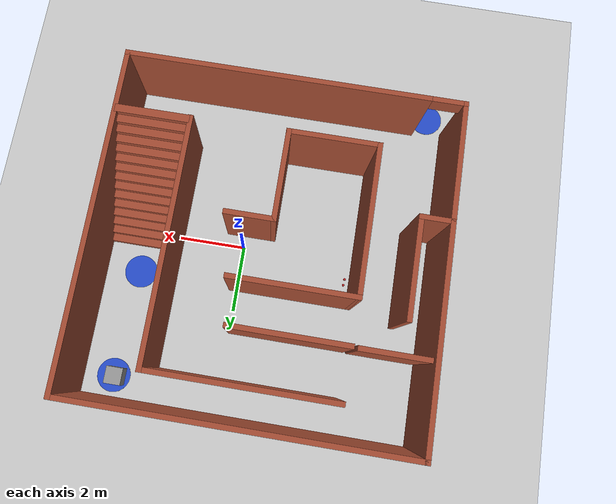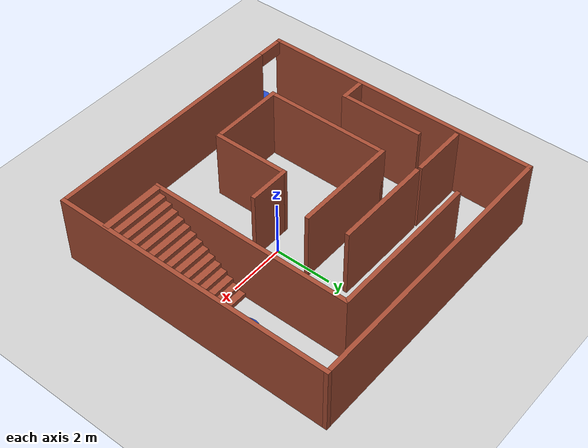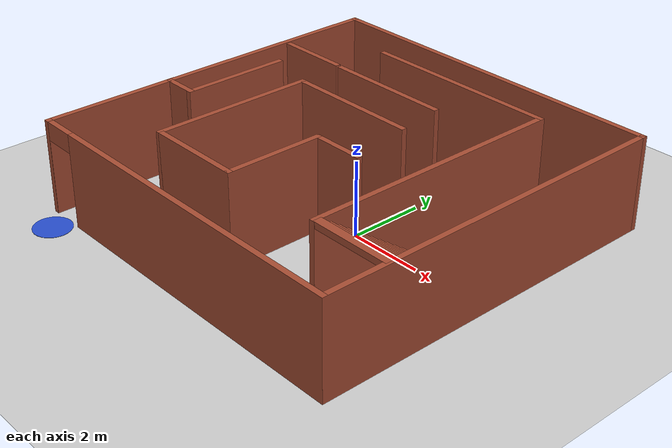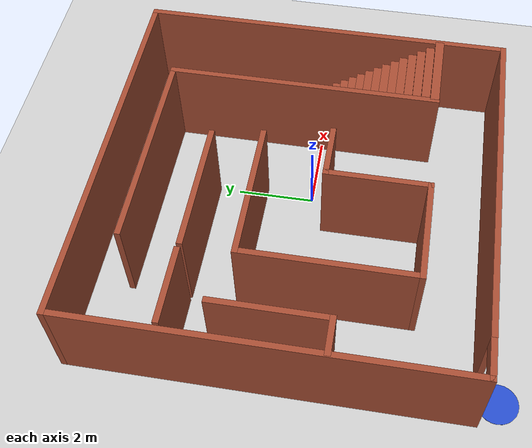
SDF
<sdf version="1.7">
 <world name="default">
  <light name="sun" type="directional">
   <pose>0 0 10 0 -0 0</pose>
   <diffuse>0.8 0.8 0.8 1</diffuse>
   <specular>0.2 0.2 0.2 1</specular>
   <attenuation>
    <range>1000</range>
    <constant>0.9</constant>
    <linear>0.01</linear>
    <quadratic>0.001</quadratic>
   </attenuation>
   <direction>-0.5 0.1 -0.9</direction>
   <spot><inner_angle>0</inner_angle><outer_angle>0</outer_angle><falloff>0</falloff></spot>
  </light>
  <model name="ground_plane">
   <static>1</static>
   <link name="link">
    <collision name="collision">
     <geometry><plane><normal>0 0 1</normal><size>100 100</size></plane></geometry>
     <surface>
      <contact><collide_bitmask>65535</collide_bitmask></contact>
      <friction><ode><mu>100</mu><mu2>50</mu2></ode></friction>
     </surface>
    </collision>
    <visual name="visual">
     <cast_shadows>0</cast_shadows>
     <geometry><plane><normal>0 0 1</normal><size>100 100</size></plane></geometry>
     <material>
      <script><uri>file://media/materials/scripts/gazebo.material</uri><name>Gazebo/Grey</name></script>
     </material>
    </visual>
   </link>
  </model>
  <gravity>0 0 -9.8</gravity>
  <magnetic_field>6e-06 2.3e-05 -4.2e-05</magnetic_field>
  <atmosphere type="adiabatic"/>
  <physics type="ode">
   <max_step_size>0.001</max_step_size>
   <real_time_factor>1</real_time_factor>
   <real_time_update_rate>1000</real_time_update_rate>
  </physics>
  <scene><ambient>0.4 0.4 0.4 1</ambient><background>0.7 0.7 0.7 1</background><shadows>1</shadows></scene>
  <audio><device>default</device></audio>
  <spherical_coordinates>
   <surface_model>EARTH_WGS84</surface_model>
   <latitude_deg>0</latitude_deg>
   <longitude_deg>0</longitude_deg>
   <elevation>0</elevation>
   <heading_deg>0</heading_deg>
  </spherical_coordinates>
  <model name="box">
   <link name="link_1">
    <inertial>
     <mass>875</mass>
     <inertia><ixx>36.4583</ixx><ixy>0</ixy><ixz>0</ixz><iyy>36.4583</iyy><iyz>0</iyz><izz>36.4583</izz></inertia>
    </inertial>
    <pose>1e-06 -5e-06 0 0 -0 0</pose>
    <visual name="visual">
     <geometry><box><size>0.5 0.5 0.5</size></box></geometry>
     <material>
      <lighting>1</lighting>
      <script><uri>file://media/materials/scripts/gazebo.material</uri><name>Gazebo/Grey</name></script>
      <shader type="pixel"><normal_map>__default__</normal_map></shader>
      <ambient>0.3 0.3 0.3 1</ambient>
      <diffuse>0.7 0.7 0.7 1</diffuse>
      <specular>0.01 0.01 0.01 1</specular>
      <emissive>0 0 0 1</emissive>
     </material>
    </visual>
    <collision name="collision">
     <geometry><box><size>0.5 0.5 0.5</size></box></geometry>
     <surface>
      <friction>
       <ode><mu>1</mu><mu2>1</mu2><fdir1>0 0 0</fdir1><slip1>0</slip1><slip2>0</slip2></ode>
       <torsional>
        <coefficient>1</coefficient>
        <patch_radius>0</patch_radius>
        <surface_radius>0</surface_radius>
        <use_patch_radius>1</use_patch_radius>
        <ode><slip>0</slip></ode>
       </torsional>
      </friction>
      <bounce><restitution_coefficient>0</restitution_coefficient><threshold>1e+06</threshold></bounce>
      <contact>
       <collide_without_contact>0</collide_without_contact>
       <collide_without_contact_bitmask>1</collide_without_contact_bitmask>
       <collide_bitmask>1</collide_bitmask>
       <ode>
        <soft_cfm>0</soft_cfm>
        <soft_erp>0.2</soft_erp>
        <kp>1e+13</kp>
        <kd>1</kd>
        <max_vel>0.01</max_vel>
        <min_depth>0</min_depth>
       </ode>
       <bullet>
        <split_impulse>1</split_impulse>
        <split_impulse_penetration_threshold>-0.01</split_impulse_penetration_threshold>
        <soft_cfm>0</soft_cfm>
        <soft_erp>0.2</soft_erp>
        <kp>1e+13</kp>
        <kd>1</kd>
       </bullet>
      </contact>
     </surface>
    </collision>
   </link>
   <static>0</static>
   <pose>3.08441 4.46812 0.255 0 -0 1e-06</pose>
  </model>
  <model name="cricket_ball">
   <link name="link">
    <pose>0 0 0.0375 0 -0 0</pose>
    <inertial>
     <mass>0.1467</mass>
     <inertia>
      <ixx>8.25187e-05</ixx>
      <ixy>0</ixy>
      <ixz>0</ixz>
      <iyy>8.25187e-05</iyy>
      <iyz>0</iyz>
      <izz>8.25187e-05</izz>
     </inertia>
    </inertial>
    <collision name="collision">
     <geometry><sphere><radius>0.0375</radius></sphere></geometry>
     <surface>
      <contact>
       <poissons_ratio>0.347</poissons_ratio>
       <elastic_modulus>8.8e+09</elastic_modulus>
       <ode><kp>100000</kp><kd>100</kd><max_vel>100</max_vel><min_depth>0.001</min_depth></ode>
      </contact>
      <friction>
       <torsional>
        <coefficient>1</coefficient>
        <use_patch_radius>0</use_patch_radius>
        <surface_radius>0.01</surface_radius>
       </torsional>
      </friction>
     </surface>
    </collision>
    <visual name="visual">
     <geometry><sphere><radius>0.0375</radius></sphere></geometry>
     <material>
      <script><uri>file://media/materials/scripts/gazebo.material</uri><name>Gazebo/Red</name></script>
     </material>
    </visual>
    <velocity_decay><linear>0</linear><angular>0.005</angular></velocity_decay>
   </link>
   <pose>-3.24488 0.467417 -0.001014 0 -0 0</pose>
  </model>
  <model name="cricket_ball_0">
   <link name="link">
    <pose>0 0 0.0375 0 -0 0</pose>
    <inertial>
     <mass>0.1467</mass>
     <inertia>
      <ixx>8.25187e-05</ixx>
      <ixy>0</ixy>
      <ixz>0</ixz>
      <iyy>8.25187e-05</iyy>
      <iyz>0</iyz>
      <izz>8.25187e-05</izz>
     </inertia>
    </inertial>
    <collision name="collision">
     <geometry><sphere><radius>0.0375</radius></sphere></geometry>
     <surface>
      <contact>
       <poissons_ratio>0.347</poissons_ratio>
       <elastic_modulus>8.8e+09</elastic_modulus>
       <ode><kp>100000</kp><kd>100</kd><max_vel>100</max_vel><min_depth>0.001</min_depth></ode>
      </contact>
      <friction>
       <torsional>
        <coefficient>1</coefficient>
        <use_patch_radius>0</use_patch_radius>
        <surface_radius>0.01</surface_radius>
       </torsional>
      </friction>
     </surface>
    </collision>
    <visual name="visual">
     <geometry><sphere><radius>0.0375</radius></sphere></geometry>
     <material>
      <script><uri>file://media/materials/scripts/gazebo.material</uri><name>Gazebo/Red</name></script>
     </material>
    </visual>
    <velocity_decay><linear>0</linear><angular>0.005</angular></velocity_decay>
   </link>
   <pose>-3.22979 0.649662 -0.001014 0 -0 0</pose>
  </model>
  <model name="Green_Circle">
   <link name="link_0">
    <inertial>
     <mass>1</mass>
     <inertia><ixx>0.145833</ixx><ixy>0</ixy><ixz>0</ixz><iyy>0.145833</iyy><iyz>0</iyz><izz>0.125</izz></inertia>
    </inertial>
    <visual name="visual">
     <geometry><cylinder><radius>0.5</radius><length>0.01</length></cylinder></geometry>
     <material>
      <lighting>1</lighting>
      <script><uri>file://media/materials/scripts/gazebo.material</uri><name>Gazebo/Blue</name></script>
      <shader type="pixel"><normal_map>__default__</normal_map></shader>
      <ambient>0.18 0.761 0.494 1</ambient>
      <diffuse>0.18 0.761 0.494 1</diffuse>
      <specular>0.18 0.761 0.494 1</specular>
      <emissive>0 0 0 1</emissive>
     </material>
    </visual>
    <collision name="collision">
     <geometry><cylinder><radius>0.5</radius><length>0.01</length></cylinder></geometry>
     <surface>
      <friction>
       <ode><mu>1</mu><mu2>1</mu2><fdir1>0 0 0</fdir1><slip1>0</slip1><slip2>0</slip2></ode>
       <torsional>
        <coefficient>1</coefficient>
        <patch_radius>0</patch_radius>
        <surface_radius>0</surface_radius>
        <use_patch_radius>1</use_patch_radius>
        <ode><slip>0</slip></ode>
       </torsional>
      </friction>
      <bounce><restitution_coefficient>0</restitution_coefficient><threshold>1e+06</threshold></bounce>
      <contact>
       <collide_without_contact>0</collide_without_contact>
       <collide_without_contact_bitmask>1</collide_without_contact_bitmask>
       <collide_bitmask>1</collide_bitmask>
       <ode>
        <soft_cfm>0</soft_cfm>
        <soft_erp>0.2</soft_erp>
        <kp>1e+13</kp>
        <kd>1</kd>
        <max_vel>0.01</max_vel>
        <min_depth>0</min_depth>
       </ode>
       <bullet>
        <split_impulse>1</split_impulse>
        <split_impulse_penetration_threshold>-0.01</split_impulse_penetration_threshold>
        <soft_cfm>0</soft_cfm>
        <soft_erp>0.2</soft_erp>
        <kp>1e+13</kp>
        <kd>1</kd>
       </bullet>
      </contact>
     </surface>
    </collision>
   </link>
   <static>1</static>
   <pose>3.18631 4.46804 0 0 -0 0</pose>
  </model>
  <model name="Red_Circle">
   <link name="link_0">
    <inertial>
     <mass>1</mass>
     <inertia><ixx>0.145833</ixx><ixy>0</ixy><ixz>0</ixz><iyy>0.145833</iyy><iyz>0</iyz><izz>0.125</izz></inertia>
    </inertial>
    <visual name="visual">
     <geometry><cylinder><radius>0.5</radius><length>0.01</length></cylinder></geometry>
     <material>
      <lighting>1</lighting>
      <script><uri>file://media/materials/scripts/gazebo.material</uri><name>Gazebo/Blue</name></script>
      <shader type="pixel"><normal_map>__default__</normal_map></shader>
      <ambient>0.753 0.11 0.157 1</ambient>
      <diffuse>0.753 0.11 0.157 1</diffuse>
      <specular>0.753 0.11 0.157 1</specular>
      <emissive>0 0 0 1</emissive>
     </material>
    </visual>
    <collision name="collision">
     <geometry><cylinder><radius>0.5</radius><length>0.01</length></cylinder></geometry>
     <surface>
      <friction>
       <ode><mu>1</mu><mu2>1</mu2><fdir1>0 0 0</fdir1><slip1>0</slip1><slip2>0</slip2></ode>
       <torsional>
        <coefficient>1</coefficient>
        <patch_radius>0</patch_radius>
        <surface_radius>0</surface_radius>
        <use_patch_radius>1</use_patch_radius>
        <ode><slip>0</slip></ode>
       </torsional>
      </friction>
      <bounce><restitution_coefficient>0</restitution_coefficient><threshold>1e+06</threshold></bounce>
      <contact>
       <collide_without_contact>0</collide_without_contact>
       <collide_without_contact_bitmask>1</collide_without_contact_bitmask>
       <collide_bitmask>1</collide_bitmask>
       <ode>
        <soft_cfm>0</soft_cfm>
        <soft_erp>0.2</soft_erp>
        <kp>1e+13</kp>
        <kd>1</kd>
        <max_vel>0.01</max_vel>
        <min_depth>0</min_depth>
       </ode>
       <bullet>
        <split_impulse>1</split_impulse>
        <split_impulse_penetration_threshold>-0.01</split_impulse_penetration_threshold>
        <soft_cfm>0</soft_cfm>
        <soft_erp>0.2</soft_erp>
        <kp>1e+13</kp>
        <kd>1</kd>
       </bullet>
      </contact>
     </surface>
    </collision>
   </link>
   <static>1</static>
   <pose>3.01972 1.24629 0 0 -0 0</pose>
  </model>
  <model name="Blue_Circle_1">
   <link name="link_0">
    <inertial>
     <mass>1</mass>
     <inertia><ixx>0.145833</ixx><ixy>0</ixy><ixz>0</ixz><iyy>0.145833</iyy><iyz>0</iyz><izz>0.125</izz></inertia>
    </inertial>
    <visual name="visual">
     <geometry><cylinder><radius>0.5</radius><length>0.01</length></cylinder></geometry>
     <material>
      <lighting>1</lighting>
      <script><uri>file://media/materials/scripts/gazebo.material</uri><name>Gazebo/Blue</name></script>
      <shader type="pixel"><normal_map>__default__</normal_map></shader>
      <ambient>0.11 0.443 0.847 1</ambient>
      <diffuse>0.11 0.443 0.847 1</diffuse>
      <specular>0.11 0.443 0.847 1</specular>
      <emissive>0 0 0 1</emissive>
     </material>
    </visual>
    <collision name="collision">
     <geometry><cylinder><radius>0.5</radius><length>0.01</length></cylinder></geometry>
     <surface>
      <friction>
       <ode><mu>1</mu><mu2>1</mu2><fdir1>0 0 0</fdir1><slip1>0</slip1><slip2>0</slip2></ode>
       <torsional>
        <coefficient>1</coefficient>
        <patch_radius>0</patch_radius>
        <surface_radius>0</surface_radius>
        <use_patch_radius>1</use_patch_radius>
        <ode><slip>0</slip></ode>
       </torsional>
      </friction>
      <bounce><restitution_coefficient>0</restitution_coefficient><threshold>1e+06</threshold></bounce>
      <contact>
       <collide_without_contact>0</collide_without_contact>
       <collide_without_contact_bitmask>1</collide_without_contact_bitmask>
       <collide_bitmask>1</collide_bitmask>
       <ode>
        <soft_cfm>0</soft_cfm>
        <soft_erp>0.2</soft_erp>
        <kp>1e+13</kp>
        <kd>1</kd>
        <max_vel>0.01</max_vel>
        <min_depth>0</min_depth>
       </ode>
       <bullet>
        <split_impulse>1</split_impulse>
        <split_impulse_penetration_threshold>-0.01</split_impulse_penetration_threshold>
        <soft_cfm>0</soft_cfm>
        <soft_erp>0.2</soft_erp>
        <kp>1e+13</kp>
        <kd>1</kd>
       </bullet>
      </contact>
     </surface>
    </collision>
   </link>
   <static>1</static>
   <pose>-5.14268 -5.21167 0 0 -0 0</pose>
  </model>
  <model name="MazeFinal">
   <link name="Stairs_0">
    <visual name="Stairs_0_Visual_0">
     <pose>3.84922 0.083239 0.083333 0 -0 0</pose>
     <geometry><box><size>2.16243 0.233333 0.166667</size></box></geometry>
     <material>
      <script><uri>file://media/materials/scripts/gazebo.material</uri><name>Gazebo/Bricks</name></script>
      <ambient>1 1 1 1</ambient>
      <shader type="pixel"/>
     </material>
     <meta><layer>0</layer></meta>
    </visual>
    <visual name="Stairs_0_Visual_1">
     <pose>3.84922 -0.150095 0.25 0 -0 0</pose>
     <geometry><box><size>2.16243 0.233333 0.166667</size></box></geometry>
     <material>
      <script><uri>file://media/materials/scripts/gazebo.material</uri><name>Gazebo/Bricks</name></script>
      <ambient>1 1 1 1</ambient>
      <shader type="pixel"/>
     </material>
     <meta><layer>0</layer></meta>
    </visual>
    <visual name="Stairs_0_Visual_2">
     <pose>3.84922 -0.383428 0.416667 0 -0 0</pose>
     <geometry><box><size>2.16243 0.233333 0.166667</size></box></geometry>
     <material>
      <script><uri>file://media/materials/scripts/gazebo.material</uri><name>Gazebo/Bricks</name></script>
      <ambient>1 1 1 1</ambient>
      <shader type="pixel"/>
     </material>
     <meta><layer>0</layer></meta>
    </visual>
    <visual name="Stairs_0_Visual_3">
     <pose>3.84922 -0.616761 0.583333 0 -0 0</pose>
     <geometry><box><size>2.16243 0.233333 0.166667</size></box></geometry>
     <material>
      <script><uri>file://media/materials/scripts/gazebo.material</uri><name>Gazebo/Bricks</name></script>
      <ambient>1 1 1 1</ambient>
      <shader type="pixel"/>
     </material>
     <meta><layer>0</layer></meta>
    </visual>
    <visual name="Stairs_0_Visual_4">
     <pose>3.84922 -0.850095 0.75 0 -0 0</pose>
     <geometry><box><size>2.16243 0.233333 0.166667</size></box></geometry>
     <material>
      <script><uri>file://media/materials/scripts/gazebo.material</uri><name>Gazebo/Bricks</name></script>
      <ambient>1 1 1 1</ambient>
      <shader type="pixel"/>
     </material>
     <meta><layer>0</layer></meta>
    </visual>
    <visual name="Stairs_0_Visual_5">
     <pose>3.84922 -1.08343 0.916667 0 -0 0</pose>
     <geometry><box><size>2.16243 0.233333 0.166667</size></box></geometry>
     <material>
      <script><uri>file://media/materials/scripts/gazebo.material</uri><name>Gazebo/Bricks</name></script>
      <ambient>1 1 1 1</ambient>
      <shader type="pixel"/>
     </material>
     <meta><layer>0</layer></meta>
    </visual>
    <visual name="Stairs_0_Visual_6">
     <pose>3.84922 -1.31676 1.08333 0 -0 0</pose>
     <geometry><box><size>2.16243 0.233333 0.166667</size></box></geometry>
     <material>
      <script><uri>file://media/materials/scripts/gazebo.material</uri><name>Gazebo/Bricks</name></script>
      <ambient>1 1 1 1</ambient>
      <shader type="pixel"/>
     </material>
     <meta><layer>0</layer></meta>
    </visual>
    <visual name="Stairs_0_Visual_7">
     <pose>3.84922 -1.5501 1.25 0 -0 0</pose>
     <geometry><box><size>2.16243 0.233333 0.166667</size></box></geometry>
     <material>
      <script><uri>file://media/materials/scripts/gazebo.material</uri><name>Gazebo/Bricks</name></script>
      <ambient>1 1 1 1</ambient>
      <shader type="pixel"/>
     </material>
     <meta><layer>0</layer></meta>
    </visual>
    <visual name="Stairs_0_Visual_8">
     <pose>3.84922 -1.78343 1.41667 0 -0 0</pose>
     <geometry><box><size>2.16243 0.233333 0.166667</size></box></geometry>
     <material>
      <script><uri>file://media/materials/scripts/gazebo.material</uri><name>Gazebo/Bricks</name></script>
      <ambient>1 1 1 1</ambient>
      <shader type="pixel"/>
     </material>
     <meta><layer>0</layer></meta>
    </visual>
    <visual name="Stairs_0_Visual_9">
     <pose>3.84922 -2.01676 1.58333 0 -0 0</pose>
     <geometry><box><size>2.16243 0.233333 0.166667</size></box></geometry>
     <material>
      <script><uri>file://media/materials/scripts/gazebo.material</uri><name>Gazebo/Bricks</name></script>
      <ambient>1 1 1 1</ambient>
      <shader type="pixel"/>
     </material>
     <meta><layer>0</layer></meta>
    </visual>
    <visual name="Stairs_0_Visual_10">
     <pose>3.84922 -2.25009 1.75 0 -0 0</pose>
     <geometry><box><size>2.16243 0.233333 0.166667</size></box></geometry>
     <material>
      <script><uri>file://media/materials/scripts/gazebo.material</uri><name>Gazebo/Bricks</name></script>
      <ambient>1 1 1 1</ambient>
      <shader type="pixel"/>
     </material>
     <meta><layer>0</layer></meta>
    </visual>
    <visual name="Stairs_0_Visual_11">
     <pose>3.84922 -2.48343 1.91667 0 -0 0</pose>
     <geometry><box><size>2.16243 0.233333 0.166667</size></box></geometry>
     <material>
      <script><uri>file://media/materials/scripts/gazebo.material</uri><name>Gazebo/Bricks</name></script>
      <ambient>1 1 1 1</ambient>
      <shader type="pixel"/>
     </material>
     <meta><layer>0</layer></meta>
    </visual>
    <visual name="Stairs_0_Visual_12">
     <pose>3.84922 -2.71676 2.08333 0 -0 0</pose>
     <geometry><box><size>2.16243 0.233333 0.166667</size></box></geometry>
     <material>
      <script><uri>file://media/materials/scripts/gazebo.material</uri><name>Gazebo/Bricks</name></script>
      <ambient>1 1 1 1</ambient>
      <shader type="pixel"/>
     </material>
     <meta><layer>0</layer></meta>
    </visual>
    <visual name="Stairs_0_Visual_13">
     <pose>3.84922 -2.9501 2.25 0 -0 0</pose>
     <geometry><box><size>2.16243 0.233333 0.166667</size></box></geometry>
     <material>
      <script><uri>file://media/materials/scripts/gazebo.material</uri><name>Gazebo/Bricks</name></script>
      <ambient>1 1 1 1</ambient>
      <shader type="pixel"/>
     </material>
     <meta><layer>0</layer></meta>
    </visual>
    <visual name="Stairs_0_Visual_14">
     <pose>3.84922 -3.18343 2.41667 0 -0 0</pose>
     <geometry><box><size>2.16243 0.233333 0.166667</size></box></geometry>
     <material>
      <script><uri>file://media/materials/scripts/gazebo.material</uri><name>Gazebo/Bricks</name></script>
      <ambient>1 1 1 1</ambient>
      <shader type="pixel"/>
     </material>
     <meta><layer>0</layer></meta>
    </visual>
    <collision name="Stairs_0_Collision_0">
     <pose>3.84922 0.083239 0.083333 0 -0 0</pose>
     <geometry><box><size>2.16243 0.233333 0.166667</size></box></geometry>
     <surface>
      <friction>
       <ode><mu>1</mu><mu2>1</mu2><fdir1>0 0 0</fdir1><slip1>0</slip1><slip2>0</slip2></ode>
       <torsional>
        <coefficient>1</coefficient>
        <patch_radius>0</patch_radius>
        <surface_radius>0</surface_radius>
        <use_patch_radius>1</use_patch_radius>
        <ode><slip>0</slip></ode>
       </torsional>
      </friction>
      <bounce><restitution_coefficient>0</restitution_coefficient><threshold>1e+06</threshold></bounce>
      <contact>
       <collide_without_contact>0</collide_without_contact>
       <collide_without_contact_bitmask>1</collide_without_contact_bitmask>
       <collide_bitmask>1</collide_bitmask>
       <ode>
        <soft_cfm>0</soft_cfm>
        <soft_erp>0.2</soft_erp>
        <kp>1e+13</kp>
        <kd>1</kd>
        <max_vel>0.01</max_vel>
        <min_depth>0</min_depth>
       </ode>
       <bullet>
        <split_impulse>1</split_impulse>
        <split_impulse_penetration_threshold>-0.01</split_impulse_penetration_threshold>
        <soft_cfm>0</soft_cfm>
        <soft_erp>0.2</soft_erp>
        <kp>1e+13</kp>
        <kd>1</kd>
       </bullet>
      </contact>
     </surface>
    </collision>
    <collision name="Stairs_0_Collision_1">
     <pose>3.84922 -0.150095 0.25 0 -0 0</pose>
     <geometry><box><size>2.16243 0.233333 0.166667</size></box></geometry>
     <surface>
      <friction>
       <ode><mu>1</mu><mu2>1</mu2><fdir1>0 0 0</fdir1><slip1>0</slip1><slip2>0</slip2></ode>
       <torsional>
        <coefficient>1</coefficient>
        <patch_radius>0</patch_radius>
        <surface_radius>0</surface_radius>
        <use_patch_radius>1</use_patch_radius>
        <ode><slip>0</slip></ode>
       </torsional>
      </friction>
      <bounce><restitution_coefficient>0</restitution_coefficient><threshold>1e+06</threshold></bounce>
      <contact>
       <collide_without_contact>0</collide_without_contact>
       <collide_without_contact_bitmask>1</collide_without_contact_bitmask>
       <collide_bitmask>1</collide_bitmask>
       <ode>
        <soft_cfm>0</soft_cfm>
        <soft_erp>0.2</soft_erp>
        <kp>1e+13</kp>
        <kd>1</kd>
        <max_vel>0.01</max_vel>
        <min_depth>0</min_depth>
       </ode>
       <bullet>
        <split_impulse>1</split_impulse>
        <split_impulse_penetration_threshold>-0.01</split_impulse_penetration_threshold>
        <soft_cfm>0</soft_cfm>
        <soft_erp>0.2</soft_erp>
        <kp>1e+13</kp>
        <kd>1</kd>
       </bullet>
      </contact>
     </surface>
    </collision>
    <collision name="Stairs_0_Collision_2">
     <pose>3.84922 -0.383428 0.416667 0 -0 0</pose>
     <geometry><box><size>2.16243 0.233333 0.166667</size></box></geometry>
     <surface>
      <friction>
       <ode><mu>1</mu><mu2>1</mu2><fdir1>0 0 0</fdir1><slip1>0</slip1><slip2>0</slip2></ode>
       <torsional>
        <coefficient>1</coefficient>
        <patch_radius>0</patch_radius>
        <surface_radius>0</surface_radius>
        <use_patch_radius>1</use_patch_radius>
        <ode><slip>0</slip></ode>
       </torsional>
      </friction>
      <bounce><restitution_coefficient>0</restitution_coefficient><threshold>1e+06</threshold></bounce>
      <contact>
       <collide_without_contact>0</collide_without_contact>
       <collide_without_contact_bitmask>1</collide_without_contact_bitmask>
       <collide_bitmask>1</collide_bitmask>
       <ode>
        <soft_cfm>0</soft_cfm>
        <soft_erp>0.2</soft_erp>
        <kp>1e+13</kp>
        <kd>1</kd>
        <max_vel>0.01</max_vel>
        <min_depth>0</min_depth>
       </ode>
       <bullet>
        <split_impulse>1</split_impulse>
        <split_impulse_penetration_threshold>-0.01</split_impulse_penetration_threshold>
        <soft_cfm>0</soft_cfm>
        <soft_erp>0.2</soft_erp>
        <kp>1e+13</kp>
        <kd>1</kd>
       </bullet>
      </contact>
     </surface>
    </collision>
    <collision name="Stairs_0_Collision_3">
     <pose>3.84922 -0.616761 0.583333 0 -0 0</pose>
     <geometry><box><size>2.16243 0.233333 0.166667</size></box></geometry>
     <surface>
      <friction>
       <ode><mu>1</mu><mu2>1</mu2><fdir1>0 0 0</fdir1><slip1>0</slip1><slip2>0</slip2></ode>
       <torsional>
        <coefficient>1</coefficient>
        <patch_radius>0</patch_radius>
        <surface_radius>0</surface_radius>
        <use_patch_radius>1</use_patch_radius>
        <ode><slip>0</slip></ode>
       </torsional>
      </friction>
      <bounce><restitution_coefficient>0</restitution_coefficient><threshold>1e+06</threshold></bounce>
      <contact>
       <collide_without_contact>0</collide_without_contact>
       <collide_without_contact_bitmask>1</collide_without_contact_bitmask>
       <collide_bitmask>1</collide_bitmask>
       <ode>
        <soft_cfm>0</soft_cfm>
        <soft_erp>0.2</soft_erp>
        <kp>1e+13</kp>
        <kd>1</kd>
        <max_vel>0.01</max_vel>
        <min_depth>0</min_depth>
       </ode>
       <bullet>
        <split_impulse>1</split_impulse>
        <split_impulse_penetration_threshold>-0.01</split_impulse_penetration_threshold>
        <soft_cfm>0</soft_cfm>
        <soft_erp>0.2</soft_erp>
        <kp>1e+13</kp>
        <kd>1</kd>
       </bullet>
      </contact>
     </surface>
    </collision>
    <collision name="Stairs_0_Collision_4">
     <pose>3.84922 -0.850095 0.75 0 -0 0</pose>
     <geometry><box><size>2.16243 0.233333 0.166667</size></box></geometry>
     <surface>
      <friction>
       <ode><mu>1</mu><mu2>1</mu2><fdir1>0 0 0</fdir1><slip1>0</slip1><slip2>0</slip2></ode>
       <torsional>
        <coefficient>1</coefficient>
        <patch_radius>0</patch_radius>
        <surface_radius>0</surface_radius>
        <use_patch_radius>1</use_patch_radius>
        <ode><slip>0</slip></ode>
       </torsional>
      </friction>
      <bounce><restitution_coefficient>0</restitution_coefficient><threshold>1e+06</threshold></bounce>
      <contact>
       <collide_without_contact>0</collide_without_contact>
       <collide_without_contact_bitmask>1</collide_without_contact_bitmask>
       <collide_bitmask>1</collide_bitmask>
       <ode>
        <soft_cfm>0</soft_cfm>
        <soft_erp>0.2</soft_erp>
        <kp>1e+13</kp>
        <kd>1</kd>
        <max_vel>0.01</max_vel>
        <min_depth>0</min_depth>
       </ode>
       <bullet>
        <split_impulse>1</split_impulse>
        <split_impulse_penetration_threshold>-0.01</split_impulse_penetration_threshold>
        <soft_cfm>0</soft_cfm>
        <soft_erp>0.2</soft_erp>
        <kp>1e+13</kp>
        <kd>1</kd>
       </bullet>
      </contact>
     </surface>
    </collision>
    <collision name="Stairs_0_Collision_5">
     <pose>3.84922 -1.08343 0.916667 0 -0 0</pose>
     <geometry><box><size>2.16243 0.233333 0.166667</size></box></geometry>
     <surface>
      <friction>
       <ode><mu>1</mu><mu2>1</mu2><fdir1>0 0 0</fdir1><slip1>0</slip1><slip2>0</slip2></ode>
       <torsional>
        <coefficient>1</coefficient>
        <patch_radius>0</patch_radius>
        <surface_radius>0</surface_radius>
        <use_patch_radius>1</use_patch_radius>
        <ode><slip>0</slip></ode>
       </torsional>
      </friction>
      <bounce><restitution_coefficient>0</restitution_coefficient><threshold>1e+06</threshold></bounce>
      <contact>
       <collide_without_contact>0</collide_without_contact>
       <collide_without_contact_bitmask>1</collide_without_contact_bitmask>
       <collide_bitmask>1</collide_bitmask>
       <ode>
        <soft_cfm>0</soft_cfm>
        <soft_erp>0.2</soft_erp>
        <kp>1e+13</kp>
        <kd>1</kd>
        <max_vel>0.01</max_vel>
        <min_depth>0</min_depth>
       </ode>
       <bullet>
        <split_impulse>1</split_impulse>
        <split_impulse_penetration_threshold>-0.01</split_impulse_penetration_threshold>
        <soft_cfm>0</soft_cfm>
        <soft_erp>0.2</soft_erp>
        <kp>1e+13</kp>
        <kd>1</kd>
       </bullet>
      </contact>
     </surface>
    </collision>
    <collision name="Stairs_0_Collision_6">
     <pose>3.84922 -1.31676 1.08333 0 -0 0</pose>
     <geometry><box><size>2.16243 0.233333 0.166667</size></box></geometry>
     <surface>
      <friction>
       <ode><mu>1</mu><mu2>1</mu2><fdir1>0 0 0</fdir1><slip1>0</slip1><slip2>0</slip2></ode>
       <torsional>
        <coefficient>1</coefficient>
        <patch_radius>0</patch_radius>
        <surface_radius>0</surface_radius>
        <use_patch_radius>1</use_patch_radius>
        <ode><slip>0</slip></ode>
       </torsional>
      </friction>
      <bounce><restitution_coefficient>0</restitution_coefficient><threshold>1e+06</threshold></bounce>
      <contact>
       <collide_without_contact>0</collide_without_contact>
       <collide_without_contact_bitmask>1</collide_without_contact_bitmask>
       <collide_bitmask>1</collide_bitmask>
       <ode>
        <soft_cfm>0</soft_cfm>
        <soft_erp>0.2</soft_erp>
        <kp>1e+13</kp>
        <kd>1</kd>
        <max_vel>0.01</max_vel>
        <min_depth>0</min_depth>
       </ode>
       <bullet>
        <split_impulse>1</split_impulse>
        <split_impulse_penetration_threshold>-0.01</split_impulse_penetration_threshold>
        <soft_cfm>0</soft_cfm>
        <soft_erp>0.2</soft_erp>
        <kp>1e+13</kp>
        <kd>1</kd>
       </bullet>
      </contact>
     </surface>
    </collision>
    <collision name="Stairs_0_Collision_7">
     <pose>3.84922 -1.5501 1.25 0 -0 0</pose>
     <geometry><box><size>2.16243 0.233333 0.166667</size></box></geometry>
     <surface>
      <friction>
       <ode><mu>1</mu><mu2>1</mu2><fdir1>0 0 0</fdir1><slip1>0</slip1><slip2>0</slip2></ode>
       <torsional>
        <coefficient>1</coefficient>
        <patch_radius>0</patch_radius>
        <surface_radius>0</surface_radius>
        <use_patch_radius>1</use_patch_radius>
        <ode><slip>0</slip></ode>
       </torsional>
      </friction>
      <bounce><restitution_coefficient>0</restitution_coefficient><threshold>1e+06</threshold></bounce>
      <contact>
       <collide_without_contact>0</collide_without_contact>
       <collide_without_contact_bitmask>1</collide_without_contact_bitmask>
       <collide_bitmask>1</collide_bitmask>
       <ode>
        <soft_cfm>0</soft_cfm>
        <soft_erp>0.2</soft_erp>
        <kp>1e+13</kp>
        <kd>1</kd>
        <max_vel>0.01</max_vel>
        <min_depth>0</min_depth>
       </ode>
       <bullet>
        <split_impulse>1</split_impulse>
        <split_impulse_penetration_threshold>-0.01</split_impulse_penetration_threshold>
        <soft_cfm>0</soft_cfm>
        <soft_erp>0.2</soft_erp>
        <kp>1e+13</kp>
        <kd>1</kd>
       </bullet>
      </contact>
     </surface>
    </collision>
    <collision name="Stairs_0_Collision_8">
     <pose>3.84922 -1.78343 1.41667 0 -0 0</pose>
     <geometry><box><size>2.16243 0.233333 0.166667</size></box></geometry>
     <surface>
      <friction>
       <ode><mu>1</mu><mu2>1</mu2><fdir1>0 0 0</fdir1><slip1>0</slip1><slip2>0</slip2></ode>
       <torsional>
        <coefficient>1</coefficient>
        <patch_radius>0</patch_radius>
        <surface_radius>0</surface_radius>
        <use_patch_radius>1</use_patch_radius>
        <ode><slip>0</slip></ode>
       </torsional>
      </friction>
      <bounce><restitution_coefficient>0</restitution_coefficient><threshold>1e+06</threshold></bounce>
      <contact>
       <collide_without_contact>0</collide_without_contact>
       <collide_without_contact_bitmask>1</collide_without_contact_bitmask>
       <collide_bitmask>1</collide_bitmask>
       <ode>
        <soft_cfm>0</soft_cfm>
        <soft_erp>0.2</soft_erp>
        <kp>1e+13</kp>
        <kd>1</kd>
        <max_vel>0.01</max_vel>
        <min_depth>0</min_depth>
       </ode>
       <bullet>
        <split_impulse>1</split_impulse>
        <split_impulse_penetration_threshold>-0.01</split_impulse_penetration_threshold>
        <soft_cfm>0</soft_cfm>
        <soft_erp>0.2</soft_erp>
        <kp>1e+13</kp>
        <kd>1</kd>
       </bullet>
      </contact>
     </surface>
    </collision>
    <collision name="Stairs_0_Collision_9">
     <pose>3.84922 -2.01676 1.58333 0 -0 0</pose>
     <geometry><box><size>2.16243 0.233333 0.166667</size></box></geometry>
     <surface>
      <friction>
       <ode><mu>1</mu><mu2>1</mu2><fdir1>0 0 0</fdir1><slip1>0</slip1><slip2>0</slip2></ode>
       <torsional>
        <coefficient>1</coefficient>
        <patch_radius>0</patch_radius>
        <surface_radius>0</surface_radius>
        <use_patch_radius>1</use_patch_radius>
        <ode><slip>0</slip></ode>
       </torsional>
      </friction>
      <bounce><restitution_coefficient>0</restitution_coefficient><threshold>1e+06</threshold></bounce>
      <contact>
       <collide_without_contact>0</collide_without_contact>
       <collide_without_contact_bitmask>1</collide_without_contact_bitmask>
       <collide_bitmask>1</collide_bitmask>
       <ode>
        <soft_cfm>0</soft_cfm>
        <soft_erp>0.2</soft_erp>
        <kp>1e+13</kp>
        <kd>1</kd>
        <max_vel>0.01</max_vel>
        <min_depth>0</min_depth>
       </ode>
       <bullet>
        <split_impulse>1</split_impulse>
        <split_impulse_penetration_threshold>-0.01</split_impulse_penetration_threshold>
        <soft_cfm>0</soft_cfm>
        <soft_erp>0.2</soft_erp>
        <kp>1e+13</kp>
        <kd>1</kd>
       </bullet>
      </contact>
     </surface>
    </collision>
    <collision name="Stairs_0_Collision_10">
     <pose>3.84922 -2.25009 1.75 0 -0 0</pose>
     <geometry><box><size>2.16243 0.233333 0.166667</size></box></geometry>
     <surface>
      <friction>
       <ode><mu>1</mu><mu2>1</mu2><fdir1>0 0 0</fdir1><slip1>0</slip1><slip2>0</slip2></ode>
       <torsional>
        <coefficient>1</coefficient>
        <patch_radius>0</patch_radius>
        <surface_radius>0</surface_radius>
        <use_patch_radius>1</use_patch_radius>
        <ode><slip>0</slip></ode>
       </torsional>
      </friction>
      <bounce><restitution_coefficient>0</restitution_coefficient><threshold>1e+06</threshold></bounce>
      <contact>
       <collide_without_contact>0</collide_without_contact>
       <collide_without_contact_bitmask>1</collide_without_contact_bitmask>
       <collide_bitmask>1</collide_bitmask>
       <ode>
        <soft_cfm>0</soft_cfm>
        <soft_erp>0.2</soft_erp>
        <kp>1e+13</kp>
        <kd>1</kd>
        <max_vel>0.01</max_vel>
        <min_depth>0</min_depth>
       </ode>
       <bullet>
        <split_impulse>1</split_impulse>
        <split_impulse_penetration_threshold>-0.01</split_impulse_penetration_threshold>
        <soft_cfm>0</soft_cfm>
        <soft_erp>0.2</soft_erp>
        <kp>1e+13</kp>
        <kd>1</kd>
       </bullet>
      </contact>
     </surface>
    </collision>
    <collision name="Stairs_0_Collision_11">
     <pose>3.84922 -2.48343 1.91667 0 -0 0</pose>
     <geometry><box><size>2.16243 0.233333 0.166667</size></box></geometry>
     <surface>
      <friction>
       <ode><mu>1</mu><mu2>1</mu2><fdir1>0 0 0</fdir1><slip1>0</slip1><slip2>0</slip2></ode>
       <torsional>
        <coefficient>1</coefficient>
        <patch_radius>0</patch_radius>
        <surface_radius>0</surface_radius>
        <use_patch_radius>1</use_patch_radius>
        <ode><slip>0</slip></ode>
       </torsional>
      </friction>
      <bounce><restitution_coefficient>0</restitution_coefficient><threshold>1e+06</threshold></bounce>
      <contact>
       <collide_without_contact>0</collide_without_contact>
       <collide_without_contact_bitmask>1</collide_without_contact_bitmask>
       <collide_bitmask>1</collide_bitmask>
       <ode>
        <soft_cfm>0</soft_cfm>
        <soft_erp>0.2</soft_erp>
        <kp>1e+13</kp>
        <kd>1</kd>
        <max_vel>0.01</max_vel>
        <min_depth>0</min_depth>
       </ode>
       <bullet>
        <split_impulse>1</split_impulse>
        <split_impulse_penetration_threshold>-0.01</split_impulse_penetration_threshold>
        <soft_cfm>0</soft_cfm>
        <soft_erp>0.2</soft_erp>
        <kp>1e+13</kp>
        <kd>1</kd>
       </bullet>
      </contact>
     </surface>
    </collision>
    <collision name="Stairs_0_Collision_12">
     <pose>3.84922 -2.71676 2.08333 0 -0 0</pose>
     <geometry><box><size>2.16243 0.233333 0.166667</size></box></geometry>
     <surface>
      <friction>
       <ode><mu>1</mu><mu2>1</mu2><fdir1>0 0 0</fdir1><slip1>0</slip1><slip2>0</slip2></ode>
       <torsional>
        <coefficient>1</coefficient>
        <patch_radius>0</patch_radius>
        <surface_radius>0</surface_radius>
        <use_patch_radius>1</use_patch_radius>
        <ode><slip>0</slip></ode>
       </torsional>
      </friction>
      <bounce><restitution_coefficient>0</restitution_coefficient><threshold>1e+06</threshold></bounce>
      <contact>
       <collide_without_contact>0</collide_without_contact>
       <collide_without_contact_bitmask>1</collide_without_contact_bitmask>
       <collide_bitmask>1</collide_bitmask>
       <ode>
        <soft_cfm>0</soft_cfm>
        <soft_erp>0.2</soft_erp>
        <kp>1e+13</kp>
        <kd>1</kd>
        <max_vel>0.01</max_vel>
        <min_depth>0</min_depth>
       </ode>
       <bullet>
        <split_impulse>1</split_impulse>
        <split_impulse_penetration_threshold>-0.01</split_impulse_penetration_threshold>
        <soft_cfm>0</soft_cfm>
        <soft_erp>0.2</soft_erp>
        <kp>1e+13</kp>
        <kd>1</kd>
       </bullet>
      </contact>
     </surface>
    </collision>
    <collision name="Stairs_0_Collision_13">
     <pose>3.84922 -2.9501 2.25 0 -0 0</pose>
     <geometry><box><size>2.16243 0.233333 0.166667</size></box></geometry>
     <surface>
      <friction>
       <ode><mu>1</mu><mu2>1</mu2><fdir1>0 0 0</fdir1><slip1>0</slip1><slip2>0</slip2></ode>
       <torsional>
        <coefficient>1</coefficient>
        <patch_radius>0</patch_radius>
        <surface_radius>0</surface_radius>
        <use_patch_radius>1</use_patch_radius>
        <ode><slip>0</slip></ode>
       </torsional>
      </friction>
      <bounce><restitution_coefficient>0</restitution_coefficient><threshold>1e+06</threshold></bounce>
      <contact>
       <collide_without_contact>0</collide_without_contact>
       <collide_without_contact_bitmask>1</collide_without_contact_bitmask>
       <collide_bitmask>1</collide_bitmask>
       <ode>
        <soft_cfm>0</soft_cfm>
        <soft_erp>0.2</soft_erp>
        <kp>1e+13</kp>
        <kd>1</kd>
        <max_vel>0.01</max_vel>
        <min_depth>0</min_depth>
       </ode>
       <bullet>
        <split_impulse>1</split_impulse>
        <split_impulse_penetration_threshold>-0.01</split_impulse_penetration_threshold>
        <soft_cfm>0</soft_cfm>
        <soft_erp>0.2</soft_erp>
        <kp>1e+13</kp>
        <kd>1</kd>
       </bullet>
      </contact>
     </surface>
    </collision>
    <collision name="Stairs_0_Collision_14">
     <pose>3.84922 -3.18343 2.41667 0 -0 0</pose>
     <geometry><box><size>2.16243 0.233333 0.166667</size></box></geometry>
     <surface>
      <friction>
       <ode><mu>1</mu><mu2>1</mu2><fdir1>0 0 0</fdir1><slip1>0</slip1><slip2>0</slip2></ode>
       <torsional>
        <coefficient>1</coefficient>
        <patch_radius>0</patch_radius>
        <surface_radius>0</surface_radius>
        <use_patch_radius>1</use_patch_radius>
        <ode><slip>0</slip></ode>
       </torsional>
      </friction>
      <bounce><restitution_coefficient>0</restitution_coefficient><threshold>1e+06</threshold></bounce>
      <contact>
       <collide_without_contact>0</collide_without_contact>
       <collide_without_contact_bitmask>1</collide_without_contact_bitmask>
       <collide_bitmask>1</collide_bitmask>
       <ode>
        <soft_cfm>0</soft_cfm>
        <soft_erp>0.2</soft_erp>
        <kp>1e+13</kp>
        <kd>1</kd>
        <max_vel>0.01</max_vel>
        <min_depth>0</min_depth>
       </ode>
       <bullet>
        <split_impulse>1</split_impulse>
        <split_impulse_penetration_threshold>-0.01</split_impulse_penetration_threshold>
        <soft_cfm>0</soft_cfm>
        <soft_erp>0.2</soft_erp>
        <kp>1e+13</kp>
        <kd>1</kd>
       </bullet>
      </contact>
     </surface>
    </collision>
   </link>
   <link name="Wall_0">
    <pose>0 -4.925 0 0 -0 0</pose>
    <visual name="Wall_0_Visual_0">
     <pose>-4.93049 0 1.25 0 -0 0</pose>
     <geometry><box><size>0.139029 0.15 2.5</size></box></geometry>
     <material>
      <script><uri>file://media/materials/scripts/gazebo.material</uri><name>Gazebo/Bricks</name></script>
      <ambient>1 1 1 1</ambient>
      <shader type="pixel"/>
     </material>
     <meta><layer>0</layer></meta>
    </visual>
    <visual name="Wall_0_Visual_1">
     <pose>0.519515 0 1.25 0 -0 0</pose>
     <geometry><box><size>8.96097 0.15 2.5</size></box></geometry>
     <material>
      <script><uri>file://media/materials/scripts/gazebo.material</uri><name>Gazebo/Bricks</name></script>
      <ambient>1 1 1 1</ambient>
      <shader type="pixel"/>
     </material>
     <meta><layer>0</layer></meta>
    </visual>
    <visual name="Wall_0_Visual_2">
     <pose>-4.41097 0 2.25 0 -0 0</pose>
     <geometry><box><size>0.9 0.15 0.5</size></box></geometry>
     <material>
      <script><uri>file://media/materials/scripts/gazebo.material</uri><name>Gazebo/Bricks</name></script>
      <ambient>1 1 1 1</ambient>
      <shader type="pixel"/>
     </material>
     <meta><layer>0</layer></meta>
    </visual>
    <collision name="Wall_0_Collision_0">
     <pose>-4.93049 0 1.25 0 -0 0</pose>
     <geometry><box><size>0.139029 0.15 2.5</size></box></geometry>
     <surface>
      <friction>
       <ode><mu>1</mu><mu2>1</mu2><fdir1>0 0 0</fdir1><slip1>0</slip1><slip2>0</slip2></ode>
       <torsional>
        <coefficient>1</coefficient>
        <patch_radius>0</patch_radius>
        <surface_radius>0</surface_radius>
        <use_patch_radius>1</use_patch_radius>
        <ode><slip>0</slip></ode>
       </torsional>
      </friction>
      <bounce><restitution_coefficient>0</restitution_coefficient><threshold>1e+06</threshold></bounce>
      <contact>
       <collide_without_contact>0</collide_without_contact>
       <collide_without_contact_bitmask>1</collide_without_contact_bitmask>
       <collide_bitmask>1</collide_bitmask>
       <ode>
        <soft_cfm>0</soft_cfm>
        <soft_erp>0.2</soft_erp>
        <kp>1e+13</kp>
        <kd>1</kd>
        <max_vel>0.01</max_vel>
        <min_depth>0</min_depth>
       </ode>
       <bullet>
        <split_impulse>1</split_impulse>
        <split_impulse_penetration_threshold>-0.01</split_impulse_penetration_threshold>
        <soft_cfm>0</soft_cfm>
        <soft_erp>0.2</soft_erp>
        <kp>1e+13</kp>
        <kd>1</kd>
       </bullet>
      </contact>
     </surface>
    </collision>
    <collision name="Wall_0_Collision_1">
     <pose>0.519515 0 1.25 0 -0 0</pose>
     <geometry><box><size>8.96097 0.15 2.5</size></box></geometry>
     <surface>
      <friction>
       <ode><mu>1</mu><mu2>1</mu2><fdir1>0 0 0</fdir1><slip1>0</slip1><slip2>0</slip2></ode>
       <torsional>
        <coefficient>1</coefficient>
        <patch_radius>0</patch_radius>
        <surface_radius>0</surface_radius>
        <use_patch_radius>1</use_patch_radius>
        <ode><slip>0</slip></ode>
       </torsional>
      </friction>
      <bounce><restitution_coefficient>0</restitution_coefficient><threshold>1e+06</threshold></bounce>
      <contact>
       <collide_without_contact>0</collide_without_contact>
       <collide_without_contact_bitmask>1</collide_without_contact_bitmask>
       <collide_bitmask>1</collide_bitmask>
       <ode>
        <soft_cfm>0</soft_cfm>
        <soft_erp>0.2</soft_erp>
        <kp>1e+13</kp>
        <kd>1</kd>
        <max_vel>0.01</max_vel>
        <min_depth>0</min_depth>
       </ode>
       <bullet>
        <split_impulse>1</split_impulse>
        <split_impulse_penetration_threshold>-0.01</split_impulse_penetration_threshold>
        <soft_cfm>0</soft_cfm>
        <soft_erp>0.2</soft_erp>
        <kp>1e+13</kp>
        <kd>1</kd>
       </bullet>
      </contact>
     </surface>
    </collision>
    <collision name="Wall_0_Collision_2">
     <pose>-4.41097 0 2.25 0 -0 0</pose>
     <geometry><box><size>0.9 0.15 0.5</size></box></geometry>
     <surface>
      <friction>
       <ode><mu>1</mu><mu2>1</mu2><fdir1>0 0 0</fdir1><slip1>0</slip1><slip2>0</slip2></ode>
       <torsional>
        <coefficient>1</coefficient>
        <patch_radius>0</patch_radius>
        <surface_radius>0</surface_radius>
        <use_patch_radius>1</use_patch_radius>
        <ode><slip>0</slip></ode>
       </torsional>
      </friction>
      <bounce><restitution_coefficient>0</restitution_coefficient><threshold>1e+06</threshold></bounce>
      <contact>
       <collide_without_contact>0</collide_without_contact>
       <collide_without_contact_bitmask>1</collide_without_contact_bitmask>
       <collide_bitmask>1</collide_bitmask>
       <ode>
        <soft_cfm>0</soft_cfm>
        <soft_erp>0.2</soft_erp>
        <kp>1e+13</kp>
        <kd>1</kd>
        <max_vel>0.01</max_vel>
        <min_depth>0</min_depth>
       </ode>
       <bullet>
        <split_impulse>1</split_impulse>
        <split_impulse_penetration_threshold>-0.01</split_impulse_penetration_threshold>
        <soft_cfm>0</soft_cfm>
        <soft_erp>0.2</soft_erp>
        <kp>1e+13</kp>
        <kd>1</kd>
       </bullet>
      </contact>
     </surface>
    </collision>
   </link>
   <link name="Wall_1">
    <pose>4.925 0 0 0 -0 1.5708</pose>
    <visual name="Wall_1_Visual">
     <pose>0 0 1.25 0 -0 0</pose>
     <geometry><box><size>10 0.15 2.5</size></box></geometry>
     <material>
      <script><uri>file://media/materials/scripts/gazebo.material</uri><name>Gazebo/Bricks</name></script>
      <ambient>1 1 1 1</ambient>
      <shader type="pixel"/>
     </material>
     <meta><layer>0</layer></meta>
    </visual>
    <collision name="Wall_1_Collision">
     <pose>0 0 1.25 0 -0 0</pose>
     <geometry><box><size>10 0.15 2.5</size></box></geometry>
     <surface>
      <friction>
       <ode><mu>1</mu><mu2>1</mu2><fdir1>0 0 0</fdir1><slip1>0</slip1><slip2>0</slip2></ode>
       <torsional>
        <coefficient>1</coefficient>
        <patch_radius>0</patch_radius>
        <surface_radius>0</surface_radius>
        <use_patch_radius>1</use_patch_radius>
        <ode><slip>0</slip></ode>
       </torsional>
      </friction>
      <bounce><restitution_coefficient>0</restitution_coefficient><threshold>1e+06</threshold></bounce>
      <contact>
       <collide_without_contact>0</collide_without_contact>
       <collide_without_contact_bitmask>1</collide_without_contact_bitmask>
       <collide_bitmask>1</collide_bitmask>
       <ode>
        <soft_cfm>0</soft_cfm>
        <soft_erp>0.2</soft_erp>
        <kp>1e+13</kp>
        <kd>1</kd>
        <max_vel>0.01</max_vel>
        <min_depth>0</min_depth>
       </ode>
       <bullet>
        <split_impulse>1</split_impulse>
        <split_impulse_penetration_threshold>-0.01</split_impulse_penetration_threshold>
        <soft_cfm>0</soft_cfm>
        <soft_erp>0.2</soft_erp>
        <kp>1e+13</kp>
        <kd>1</kd>
       </bullet>
      </contact>
     </surface>
    </collision>
   </link>
   <link name="Wall_10">
    <pose>-0.96091 2.36545 0 0 -0 0</pose>
    <visual name="Wall_10_Visual">
     <pose>0 0 1.25 0 -0 0</pose>
     <geometry><box><size>3.5 0.15 2.5</size></box></geometry>
     <material>
      <script><uri>file://media/materials/scripts/gazebo.material</uri><name>Gazebo/Bricks</name></script>
      <ambient>1 1 1 1</ambient>
      <shader type="pixel"/>
     </material>
     <meta><layer>0</layer></meta>
    </visual>
    <collision name="Wall_10_Collision">
     <pose>0 0 1.25 0 -0 0</pose>
     <geometry><box><size>3.5 0.15 2.5</size></box></geometry>
     <surface>
      <friction>
       <ode><mu>1</mu><mu2>1</mu2><fdir1>0 0 0</fdir1><slip1>0</slip1><slip2>0</slip2></ode>
       <torsional>
        <coefficient>1</coefficient>
        <patch_radius>0</patch_radius>
        <surface_radius>0</surface_radius>
        <use_patch_radius>1</use_patch_radius>
        <ode><slip>0</slip></ode>
       </torsional>
      </friction>
      <bounce><restitution_coefficient>0</restitution_coefficient><threshold>1e+06</threshold></bounce>
      <contact>
       <collide_without_contact>0</collide_without_contact>
       <collide_without_contact_bitmask>1</collide_without_contact_bitmask>
       <collide_bitmask>1</collide_bitmask>
       <ode>
        <soft_cfm>0</soft_cfm>
        <soft_erp>0.2</soft_erp>
        <kp>1e+13</kp>
        <kd>1</kd>
        <max_vel>0.01</max_vel>
        <min_depth>0</min_depth>
       </ode>
       <bullet>
        <split_impulse>1</split_impulse>
        <split_impulse_penetration_threshold>-0.01</split_impulse_penetration_threshold>
        <soft_cfm>0</soft_cfm>
        <soft_erp>0.2</soft_erp>
        <kp>1e+13</kp>
        <kd>1</kd>
       </bullet>
      </contact>
     </surface>
    </collision>
   </link>
   <link name="Wall_13">
    <pose>0.06968 3.86438 0 0 -0 0</pose>
    <visual name="Wall_13_Visual">
     <pose>0 0 1.25 0 -0 0</pose>
     <geometry><box><size>5.5 0.15 2.5</size></box></geometry>
     <material>
      <script><uri>file://media/materials/scripts/gazebo.material</uri><name>Gazebo/Bricks</name></script>
      <ambient>1 1 1 1</ambient>
      <shader type="pixel"/>
     </material>
     <meta><layer>0</layer></meta>
    </visual>
    <collision name="Wall_13_Collision">
     <pose>0 0 1.25 0 -0 0</pose>
     <geometry><box><size>5.5 0.15 2.5</size></box></geometry>
     <surface>
      <friction>
       <ode><mu>1</mu><mu2>1</mu2><fdir1>0 0 0</fdir1><slip1>0</slip1><slip2>0</slip2></ode>
       <torsional>
        <coefficient>1</coefficient>
        <patch_radius>0</patch_radius>
        <surface_radius>0</surface_radius>
        <use_patch_radius>1</use_patch_radius>
        <ode><slip>0</slip></ode>
       </torsional>
      </friction>
      <bounce><restitution_coefficient>0</restitution_coefficient><threshold>1e+06</threshold></bounce>
      <contact>
       <collide_without_contact>0</collide_without_contact>
       <collide_without_contact_bitmask>1</collide_without_contact_bitmask>
       <collide_bitmask>1</collide_bitmask>
       <ode>
        <soft_cfm>0</soft_cfm>
        <soft_erp>0.2</soft_erp>
        <kp>1e+13</kp>
        <kd>1</kd>
        <max_vel>0.01</max_vel>
        <min_depth>0</min_depth>
       </ode>
       <bullet>
        <split_impulse>1</split_impulse>
        <split_impulse_penetration_threshold>-0.01</split_impulse_penetration_threshold>
        <soft_cfm>0</soft_cfm>
        <soft_erp>0.2</soft_erp>
        <kp>1e+13</kp>
        <kd>1</kd>
       </bullet>
      </contact>
     </surface>
    </collision>
   </link>
   <link name="Wall_14">
    <pose>2.74468 0.314376 0 0 0 -1.5708</pose>
    <visual name="Wall_14_Visual">
     <pose>0 0 1.25 0 -0 0</pose>
     <geometry><box><size>7.25 0.15 2.5</size></box></geometry>
     <material>
      <script><uri>file://media/materials/scripts/gazebo.material</uri><name>Gazebo/Bricks</name></script>
      <ambient>1 1 1 1</ambient>
      <shader type="pixel"/>
     </material>
     <meta><layer>0</layer></meta>
    </visual>
    <collision name="Wall_14_Collision">
     <pose>0 0 1.25 0 -0 0</pose>
     <geometry><box><size>7.25 0.15 2.5</size></box></geometry>
     <surface>
      <friction>
       <ode><mu>1</mu><mu2>1</mu2><fdir1>0 0 0</fdir1><slip1>0</slip1><slip2>0</slip2></ode>
       <torsional>
        <coefficient>1</coefficient>
        <patch_radius>0</patch_radius>
        <surface_radius>0</surface_radius>
        <use_patch_radius>1</use_patch_radius>
        <ode><slip>0</slip></ode>
       </torsional>
      </friction>
      <bounce><restitution_coefficient>0</restitution_coefficient><threshold>1e+06</threshold></bounce>
      <contact>
       <collide_without_contact>0</collide_without_contact>
       <collide_without_contact_bitmask>1</collide_without_contact_bitmask>
       <collide_bitmask>1</collide_bitmask>
       <ode>
        <soft_cfm>0</soft_cfm>
        <soft_erp>0.2</soft_erp>
        <kp>1e+13</kp>
        <kd>1</kd>
        <max_vel>0.01</max_vel>
        <min_depth>0</min_depth>
       </ode>
       <bullet>
        <split_impulse>1</split_impulse>
        <split_impulse_penetration_threshold>-0.01</split_impulse_penetration_threshold>
        <soft_cfm>0</soft_cfm>
        <soft_erp>0.2</soft_erp>
        <kp>1e+13</kp>
        <kd>1</kd>
       </bullet>
      </contact>
     </surface>
    </collision>
   </link>
   <link name="Wall_16">
    <pose>-1.36922 -3.29308 0 0 -0 0</pose>
    <visual name="Wall_16_Visual">
     <pose>0 0 1.25 0 -0 0</pose>
     <geometry><box><size>2.75 0.15 2.5</size></box></geometry>
     <material>
      <script><uri>file://media/materials/scripts/gazebo.material</uri><name>Gazebo/Bricks</name></script>
      <ambient>1 1 1 1</ambient>
      <shader type="pixel"/>
     </material>
     <meta><layer>0</layer></meta>
    </visual>
    <collision name="Wall_16_Collision">
     <pose>0 0 1.25 0 -0 0</pose>
     <geometry><box><size>2.75 0.15 2.5</size></box></geometry>
     <surface>
      <friction>
       <ode><mu>1</mu><mu2>1</mu2><fdir1>0 0 0</fdir1><slip1>0</slip1><slip2>0</slip2></ode>
       <torsional>
        <coefficient>1</coefficient>
        <patch_radius>0</patch_radius>
        <surface_radius>0</surface_radius>
        <use_patch_radius>1</use_patch_radius>
        <ode><slip>0</slip></ode>
       </torsional>
      </friction>
      <bounce><restitution_coefficient>0</restitution_coefficient><threshold>1e+06</threshold></bounce>
      <contact>
       <collide_without_contact>0</collide_without_contact>
       <collide_without_contact_bitmask>1</collide_without_contact_bitmask>
       <collide_bitmask>1</collide_bitmask>
       <ode>
        <soft_cfm>0</soft_cfm>
        <soft_erp>0.2</soft_erp>
        <kp>1e+13</kp>
        <kd>1</kd>
        <max_vel>0.01</max_vel>
        <min_depth>0</min_depth>
       </ode>
       <bullet>
        <split_impulse>1</split_impulse>
        <split_impulse_penetration_threshold>-0.01</split_impulse_penetration_threshold>
        <soft_cfm>0</soft_cfm>
        <soft_erp>0.2</soft_erp>
        <kp>1e+13</kp>
        <kd>1</kd>
       </bullet>
      </contact>
     </surface>
    </collision>
   </link>
   <link name="Wall_17">
    <pose>-0.069221 -1.99307 0 0 -0 1.5708</pose>
    <visual name="Wall_17_Visual">
     <pose>0 0 1.25 0 -0 0</pose>
     <geometry><box><size>2.75 0.15 2.5</size></box></geometry>
     <material>
      <script><uri>file://media/materials/scripts/gazebo.material</uri><name>Gazebo/Bricks</name></script>
      <ambient>1 1 1 1</ambient>
      <shader type="pixel"/>
     </material>
     <meta><layer>0</layer></meta>
    </visual>
    <collision name="Wall_17_Collision">
     <pose>0 0 1.25 0 -0 0</pose>
     <geometry><box><size>2.75 0.15 2.5</size></box></geometry>
     <surface>
      <friction>
       <ode><mu>1</mu><mu2>1</mu2><fdir1>0 0 0</fdir1><slip1>0</slip1><slip2>0</slip2></ode>
       <torsional>
        <coefficient>1</coefficient>
        <patch_radius>0</patch_radius>
        <surface_radius>0</surface_radius>
        <use_patch_radius>1</use_patch_radius>
        <ode><slip>0</slip></ode>
       </torsional>
      </friction>
      <bounce><restitution_coefficient>0</restitution_coefficient><threshold>1e+06</threshold></bounce>
      <contact>
       <collide_without_contact>0</collide_without_contact>
       <collide_without_contact_bitmask>1</collide_without_contact_bitmask>
       <collide_bitmask>1</collide_bitmask>
       <ode>
        <soft_cfm>0</soft_cfm>
        <soft_erp>0.2</soft_erp>
        <kp>1e+13</kp>
        <kd>1</kd>
        <max_vel>0.01</max_vel>
        <min_depth>0</min_depth>
       </ode>
       <bullet>
        <split_impulse>1</split_impulse>
        <split_impulse_penetration_threshold>-0.01</split_impulse_penetration_threshold>
        <soft_cfm>0</soft_cfm>
        <soft_erp>0.2</soft_erp>
        <kp>1e+13</kp>
        <kd>1</kd>
       </bullet>
      </contact>
     </surface>
    </collision>
   </link>
   <link name="Wall_18">
    <pose>0.605779 -0.693076 0 0 -0 0</pose>
    <visual name="Wall_18_Visual">
     <pose>0 0 1.25 0 -0 0</pose>
     <geometry><box><size>1.5 0.15 2.5</size></box></geometry>
     <material>
      <script><uri>file://media/materials/scripts/gazebo.material</uri><name>Gazebo/Bricks</name></script>
      <ambient>1 1 1 1</ambient>
      <shader type="pixel"/>
     </material>
     <meta><layer>0</layer></meta>
    </visual>
    <collision name="Wall_18_Collision">
     <pose>0 0 1.25 0 -0 0</pose>
     <geometry><box><size>1.5 0.15 2.5</size></box></geometry>
     <surface>
      <friction>
       <ode><mu>1</mu><mu2>1</mu2><fdir1>0 0 0</fdir1><slip1>0</slip1><slip2>0</slip2></ode>
       <torsional>
        <coefficient>1</coefficient>
        <patch_radius>0</patch_radius>
        <surface_radius>0</surface_radius>
        <use_patch_radius>1</use_patch_radius>
        <ode><slip>0</slip></ode>
       </torsional>
      </friction>
      <bounce><restitution_coefficient>0</restitution_coefficient><threshold>1e+06</threshold></bounce>
      <contact>
       <collide_without_contact>0</collide_without_contact>
       <collide_without_contact_bitmask>1</collide_without_contact_bitmask>
       <collide_bitmask>1</collide_bitmask>
       <ode>
        <soft_cfm>0</soft_cfm>
        <soft_erp>0.2</soft_erp>
        <kp>1e+13</kp>
        <kd>1</kd>
        <max_vel>0.01</max_vel>
        <min_depth>0</min_depth>
       </ode>
       <bullet>
        <split_impulse>1</split_impulse>
        <split_impulse_penetration_threshold>-0.01</split_impulse_penetration_threshold>
        <soft_cfm>0</soft_cfm>
        <soft_erp>0.2</soft_erp>
        <kp>1e+13</kp>
        <kd>1</kd>
       </bullet>
      </contact>
     </surface>
    </collision>
   </link>
   <link name="Wall_2">
    <pose>0 4.925 0 0 -0 3.14159</pose>
    <inertial>
     <mass>1</mass>
     <inertia><ixx>1</ixx><ixy>0</ixy><ixz>0</ixz><iyy>1</iyy><iyz>0</iyz><izz>1</izz></inertia>
    </inertial>
    <visual name="Wall_2_Visual">
     <pose>0 0 1.25 0 -0 0</pose>
     <geometry><box><size>10 0.15 2.5</size></box></geometry>
     <material>
      <script><uri>file://media/materials/scripts/gazebo.material</uri><name>Gazebo/Bricks</name></script>
      <ambient>1 1 1 1</ambient>
      <shader type="pixel"><normal_map>__default__</normal_map></shader>
     </material>
     <meta><layer>0</layer></meta>
    </visual>
    <collision name="Wall_2_Collision">
     <pose>0 0 1.25 0 -0 0</pose>
     <geometry><box><size>10 0.15 2.5</size></box></geometry>
     <surface>
      <friction>
       <ode><mu>1</mu><mu2>1</mu2><fdir1>0 0 0</fdir1><slip1>0</slip1><slip2>0</slip2></ode>
       <torsional>
        <coefficient>1</coefficient>
        <patch_radius>0</patch_radius>
        <surface_radius>0</surface_radius>
        <use_patch_radius>1</use_patch_radius>
        <ode><slip>0</slip></ode>
       </torsional>
      </friction>
      <bounce><restitution_coefficient>0</restitution_coefficient><threshold>1e+06</threshold></bounce>
      <contact>
       <collide_without_contact>0</collide_without_contact>
       <collide_without_contact_bitmask>1</collide_without_contact_bitmask>
       <collide_bitmask>1</collide_bitmask>
       <ode>
        <soft_cfm>0</soft_cfm>
        <soft_erp>0.2</soft_erp>
        <kp>1e+13</kp>
        <kd>1</kd>
        <max_vel>0.01</max_vel>
        <min_depth>0</min_depth>
       </ode>
       <bullet>
        <split_impulse>1</split_impulse>
        <split_impulse_penetration_threshold>-0.01</split_impulse_penetration_threshold>
        <soft_cfm>0</soft_cfm>
        <soft_erp>0.2</soft_erp>
        <kp>1e+13</kp>
        <kd>1</kd>
       </bullet>
      </contact>
     </surface>
    </collision>
   </link>
   <link name="Wall_20">
    <pose>-4.47459 -1.42773 0 0 -0 0</pose>
    <visual name="Wall_20_Visual">
     <pose>0 0 1.25 0 -0 0</pose>
     <geometry><box><size>1 0.15 2.5</size></box></geometry>
     <material>
      <script><uri>file://media/materials/scripts/gazebo.material</uri><name>Gazebo/Bricks</name></script>
      <ambient>1 1 1 1</ambient>
      <shader type="pixel"/>
     </material>
     <meta><layer>0</layer></meta>
    </visual>
    <collision name="Wall_20_Collision">
     <pose>0 0 1.25 0 -0 0</pose>
     <geometry><box><size>1 0.15 2.5</size></box></geometry>
     <surface>
      <friction>
       <ode><mu>1</mu><mu2>1</mu2><fdir1>0 0 0</fdir1><slip1>0</slip1><slip2>0</slip2></ode>
       <torsional>
        <coefficient>1</coefficient>
        <patch_radius>0</patch_radius>
        <surface_radius>0</surface_radius>
        <use_patch_radius>1</use_patch_radius>
        <ode><slip>0</slip></ode>
       </torsional>
      </friction>
      <bounce><restitution_coefficient>0</restitution_coefficient><threshold>1e+06</threshold></bounce>
      <contact>
       <collide_without_contact>0</collide_without_contact>
       <collide_without_contact_bitmask>1</collide_without_contact_bitmask>
       <collide_bitmask>1</collide_bitmask>
       <ode>
        <soft_cfm>0</soft_cfm>
        <soft_erp>0.2</soft_erp>
        <kp>1e+13</kp>
        <kd>1</kd>
        <max_vel>0.01</max_vel>
        <min_depth>0</min_depth>
       </ode>
       <bullet>
        <split_impulse>1</split_impulse>
        <split_impulse_penetration_threshold>-0.01</split_impulse_penetration_threshold>
        <soft_cfm>0</soft_cfm>
        <soft_erp>0.2</soft_erp>
        <kp>1e+13</kp>
        <kd>1</kd>
       </bullet>
      </contact>
     </surface>
    </collision>
   </link>
   <link name="Wall_21">
    <pose>-4.04959 -0.002734 0 0 -0 1.5708</pose>
    <visual name="Wall_21_Visual">
     <pose>0 0 1.25 0 -0 0</pose>
     <geometry><box><size>3 0.15 2.5</size></box></geometry>
     <material>
      <script><uri>file://media/materials/scripts/gazebo.material</uri><name>Gazebo/Bricks</name></script>
      <ambient>1 1 1 1</ambient>
      <shader type="pixel"/>
     </material>
     <meta><layer>0</layer></meta>
    </visual>
    <collision name="Wall_21_Collision">
     <pose>0 0 1.25 0 -0 0</pose>
     <geometry><box><size>3 0.15 2.5</size></box></geometry>
     <surface>
      <friction>
       <ode><mu>1</mu><mu2>1</mu2><fdir1>0 0 0</fdir1><slip1>0</slip1><slip2>0</slip2></ode>
       <torsional>
        <coefficient>1</coefficient>
        <patch_radius>0</patch_radius>
        <surface_radius>0</surface_radius>
        <use_patch_radius>1</use_patch_radius>
        <ode><slip>0</slip></ode>
       </torsional>
      </friction>
      <bounce><restitution_coefficient>0</restitution_coefficient><threshold>1e+06</threshold></bounce>
      <contact>
       <collide_without_contact>0</collide_without_contact>
       <collide_without_contact_bitmask>1</collide_without_contact_bitmask>
       <collide_bitmask>1</collide_bitmask>
       <ode>
        <soft_cfm>0</soft_cfm>
        <soft_erp>0.2</soft_erp>
        <kp>1e+13</kp>
        <kd>1</kd>
        <max_vel>0.01</max_vel>
        <min_depth>0</min_depth>
       </ode>
       <bullet>
        <split_impulse>1</split_impulse>
        <split_impulse_penetration_threshold>-0.01</split_impulse_penetration_threshold>
        <soft_cfm>0</soft_cfm>
        <soft_erp>0.2</soft_erp>
        <kp>1e+13</kp>
        <kd>1</kd>
       </bullet>
      </contact>
     </surface>
    </collision>
   </link>
   <link name="Wall_3">
    <pose>-4.925 0 0 0 0 -1.5708</pose>
    <visual name="Wall_3_Visual">
     <pose>0 0 1.25 0 -0 0</pose>
     <geometry><box><size>10 0.15 2.5</size></box></geometry>
     <material>
      <script><uri>file://media/materials/scripts/gazebo.material</uri><name>Gazebo/Bricks</name></script>
      <ambient>1 1 1 1</ambient>
      <shader type="pixel"/>
     </material>
     <meta><layer>0</layer></meta>
    </visual>
    <collision name="Wall_3_Collision">
     <pose>0 0 1.25 0 -0 0</pose>
     <geometry><box><size>10 0.15 2.5</size></box></geometry>
     <surface>
      <friction>
       <ode><mu>1</mu><mu2>1</mu2><fdir1>0 0 0</fdir1><slip1>0</slip1><slip2>0</slip2></ode>
       <torsional>
        <coefficient>1</coefficient>
        <patch_radius>0</patch_radius>
        <surface_radius>0</surface_radius>
        <use_patch_radius>1</use_patch_radius>
        <ode><slip>0</slip></ode>
       </torsional>
      </friction>
      <bounce><restitution_coefficient>0</restitution_coefficient><threshold>1e+06</threshold></bounce>
      <contact>
       <collide_without_contact>0</collide_without_contact>
       <collide_without_contact_bitmask>1</collide_without_contact_bitmask>
       <collide_bitmask>1</collide_bitmask>
       <ode>
        <soft_cfm>0</soft_cfm>
        <soft_erp>0.2</soft_erp>
        <kp>1e+13</kp>
        <kd>1</kd>
        <max_vel>0.01</max_vel>
        <min_depth>0</min_depth>
       </ode>
       <bullet>
        <split_impulse>1</split_impulse>
        <split_impulse_penetration_threshold>-0.01</split_impulse_penetration_threshold>
        <soft_cfm>0</soft_cfm>
        <soft_erp>0.2</soft_erp>
        <kp>1e+13</kp>
        <kd>1</kd>
       </bullet>
      </contact>
     </surface>
    </collision>
   </link>
   <link name="Wall_7">
    <pose>-2.66922 -1.11808 0 0 -0 1.5708</pose>
    <visual name="Wall_7_Visual">
     <pose>0 0 1.25 0 -0 0</pose>
     <geometry><box><size>4.5 0.15 2.5</size></box></geometry>
     <material>
      <script><uri>file://media/materials/scripts/gazebo.material</uri><name>Gazebo/Bricks</name></script>
      <ambient>1 1 1 1</ambient>
      <shader type="pixel"/>
     </material>
     <meta><layer>0</layer></meta>
    </visual>
    <collision name="Wall_7_Collision">
     <pose>0 0 1.25 0 -0 0</pose>
     <geometry><box><size>4.5 0.15 2.5</size></box></geometry>
     <surface>
      <friction>
       <ode><mu>1</mu><mu2>1</mu2><fdir1>0 0 0</fdir1><slip1>0</slip1><slip2>0</slip2></ode>
       <torsional>
        <coefficient>1</coefficient>
        <patch_radius>0</patch_radius>
        <surface_radius>0</surface_radius>
        <use_patch_radius>1</use_patch_radius>
        <ode><slip>0</slip></ode>
       </torsional>
      </friction>
      <bounce><restitution_coefficient>0</restitution_coefficient><threshold>1e+06</threshold></bounce>
      <contact>
       <collide_without_contact>0</collide_without_contact>
       <collide_without_contact_bitmask>1</collide_without_contact_bitmask>
       <collide_bitmask>1</collide_bitmask>
       <ode>
        <soft_cfm>0</soft_cfm>
        <soft_erp>0.2</soft_erp>
        <kp>1e+13</kp>
        <kd>1</kd>
        <max_vel>0.01</max_vel>
        <min_depth>0</min_depth>
       </ode>
       <bullet>
        <split_impulse>1</split_impulse>
        <split_impulse_penetration_threshold>-0.01</split_impulse_penetration_threshold>
        <soft_cfm>0</soft_cfm>
        <soft_erp>0.2</soft_erp>
        <kp>1e+13</kp>
        <kd>1</kd>
       </bullet>
      </contact>
     </surface>
    </collision>
   </link>
   <link name="Wall_8">
    <pose>-0.869221 1.05692 0 0 -0 0</pose>
    <visual name="Wall_8_Visual">
     <pose>0 0 1.25 0 -0 0</pose>
     <geometry><box><size>3.75 0.15 2.5</size></box></geometry>
     <material>
      <script><uri>file://media/materials/scripts/gazebo.material</uri><name>Gazebo/Bricks</name></script>
      <ambient>1 1 1 1</ambient>
      <shader type="pixel"/>
     </material>
     <meta><layer>0</layer></meta>
    </visual>
    <collision name="Wall_8_Collision">
     <pose>0 0 1.25 0 -0 0</pose>
     <geometry><box><size>3.75 0.15 2.5</size></box></geometry>
     <surface>
      <friction>
       <ode><mu>1</mu><mu2>1</mu2><fdir1>0 0 0</fdir1><slip1>0</slip1><slip2>0</slip2></ode>
       <torsional>
        <coefficient>1</coefficient>
        <patch_radius>0</patch_radius>
        <surface_radius>0</surface_radius>
        <use_patch_radius>1</use_patch_radius>
        <ode><slip>0</slip></ode>
       </torsional>
      </friction>
      <bounce><restitution_coefficient>0</restitution_coefficient><threshold>1e+06</threshold></bounce>
      <contact>
       <collide_without_contact>0</collide_without_contact>
       <collide_without_contact_bitmask>1</collide_without_contact_bitmask>
       <collide_bitmask>1</collide_bitmask>
       <ode>
        <soft_cfm>0</soft_cfm>
        <soft_erp>0.2</soft_erp>
        <kp>1e+13</kp>
        <kd>1</kd>
        <max_vel>0.01</max_vel>
        <min_depth>0</min_depth>
       </ode>
       <bullet>
        <split_impulse>1</split_impulse>
        <split_impulse_penetration_threshold>-0.01</split_impulse_penetration_threshold>
        <soft_cfm>0</soft_cfm>
        <soft_erp>0.2</soft_erp>
        <kp>1e+13</kp>
        <kd>1</kd>
       </bullet>
      </contact>
     </surface>
    </collision>
   </link>
   <static>1</static>
   <pose>-0.785 0.245 0 0 -0 0</pose>
  </model>
  <model name="walltest2">
   <pose>-1.19528 5.24996 0 0 -0 0</pose>
   <link name="Wall_7">
    <collision name="Wall_7_Collision">
     <geometry><box><size>2 0.15 2.5</size></box></geometry>
     <pose>0 0 1.25 0 -0 0</pose>
    </collision>
    <visual name="Wall_7_Visual">
     <pose>0 0 1.25 0 -0 0</pose>
     <geometry><box><size>2 0.15 2.5</size></box></geometry>
     <material>
      <script><uri>file://media/materials/scripts/gazebo.material</uri><name>Gazebo/Bricks</name></script>
      <ambient>1 1 1 1</ambient>
     </material>
     <meta><layer>0</layer></meta>
    </visual>
    <pose>-3.38374 -2.6187 0 0 -0 3.14159</pose>
   </link>
   <static>1</static>
  </model>
 </world>
</sdf>
